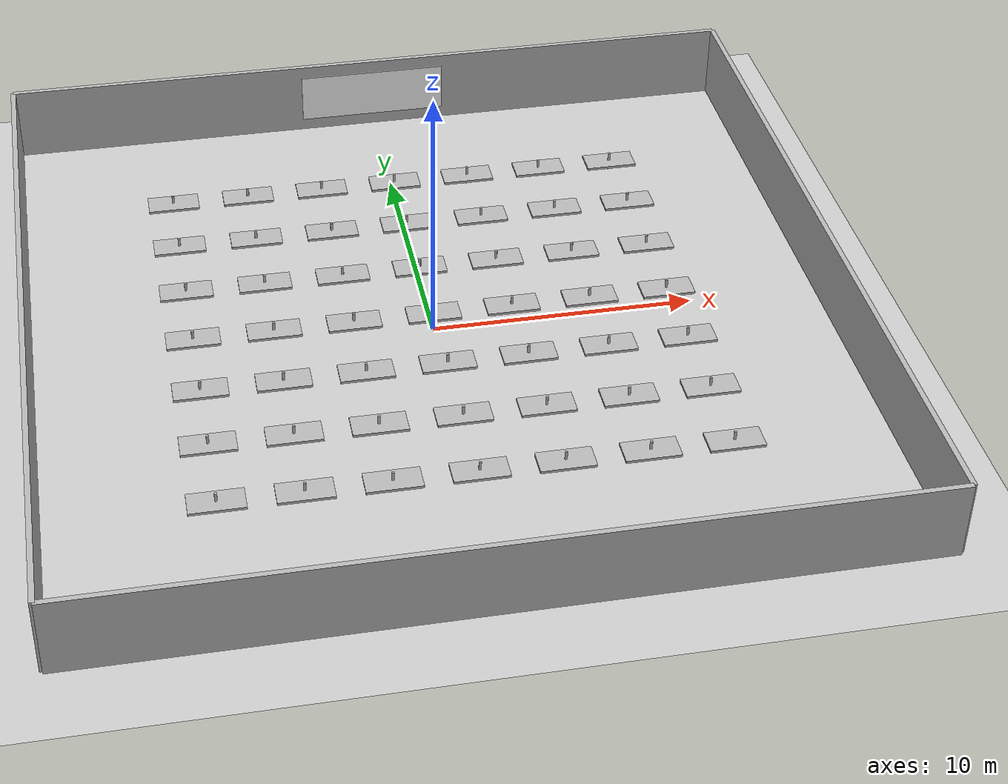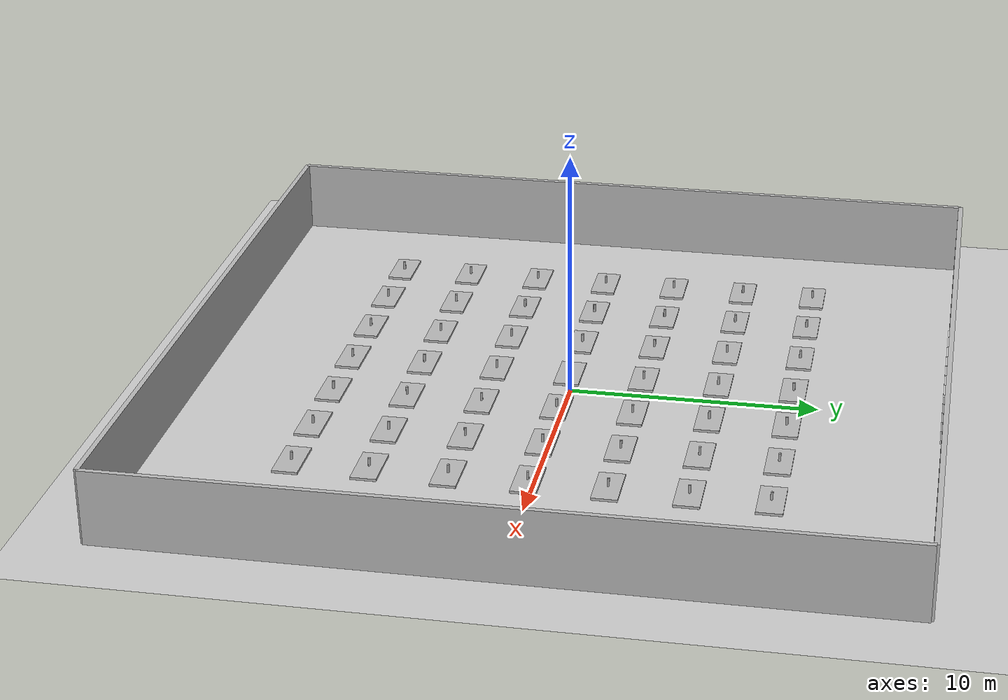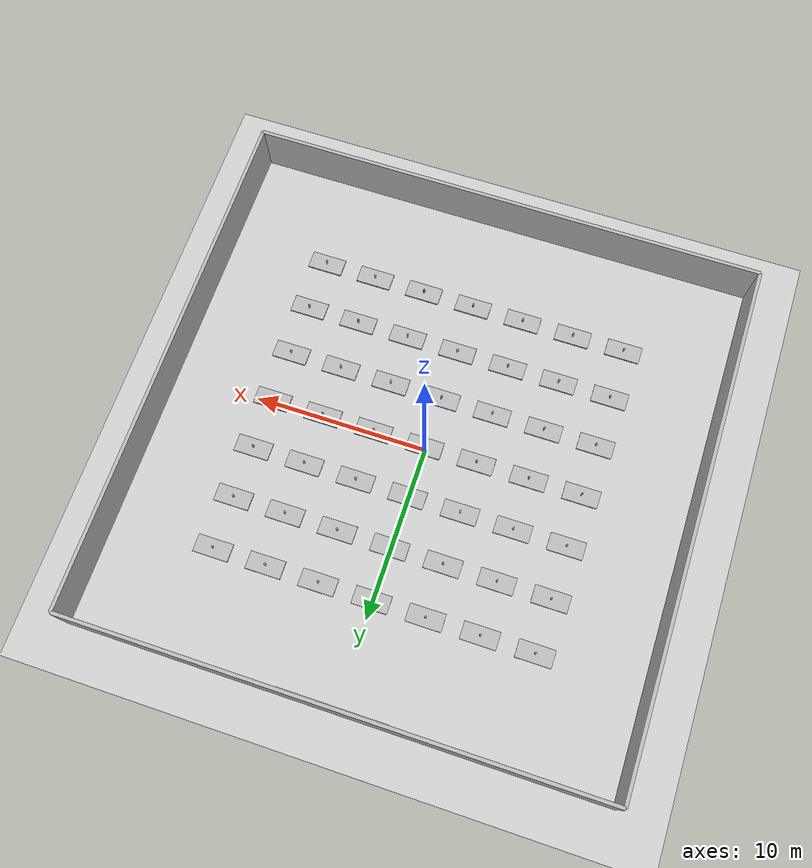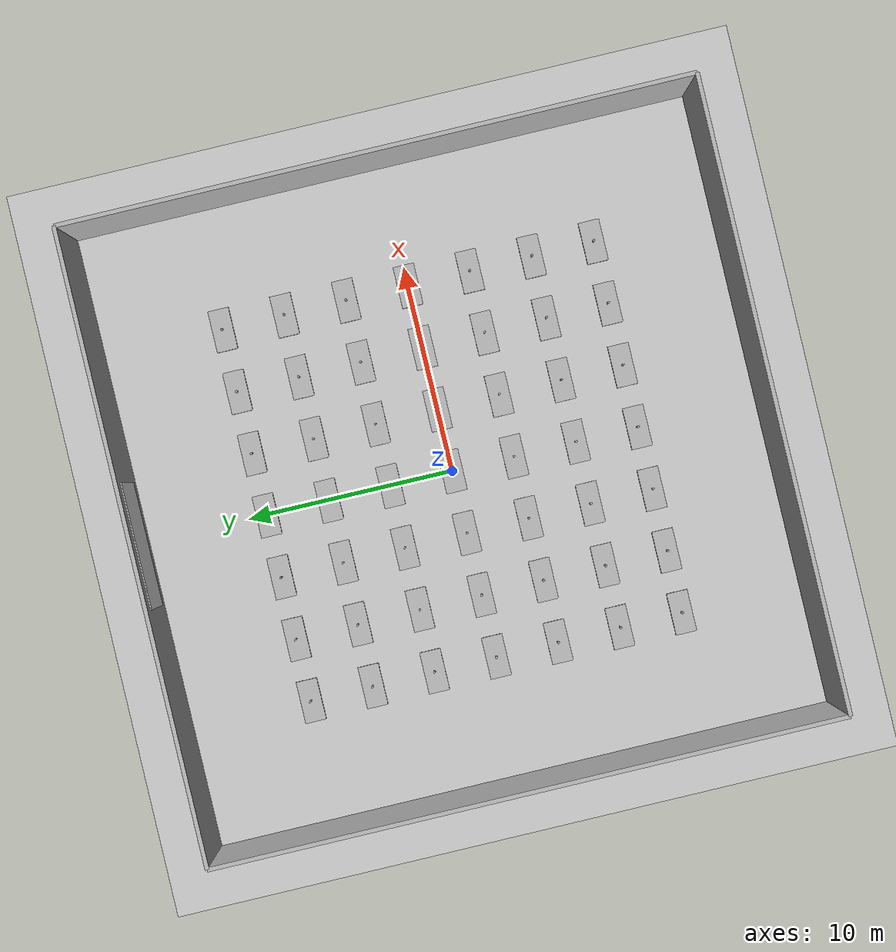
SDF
<sdf version="1.7">
 <world name="classroom_world">
  <light name="sun" type="directional">
   <pose>0 0 10 0 -0 0</pose>
   <diffuse>0.8 0.8 0.8 1</diffuse>
   <specular>0.2 0.2 0.2 1</specular>
   <attenuation>
    <range>1000</range>
    <constant>0.9</constant>
    <linear>0.01</linear>
    <quadratic>0.001</quadratic>
   </attenuation>
   <direction>-0.5 0.1 -0.9</direction>
   <spot><inner_angle>0</inner_angle><outer_angle>0</outer_angle><falloff>0</falloff></spot>
  </light>
  <model name="ground_plane">
   <static>1</static>
   <link name="link">
    <collision name="collision">
     <geometry><plane><normal>0 0 1</normal><size>100 100</size></plane></geometry>
     <surface><friction><ode><mu>100</mu><mu2>50</mu2></ode></friction></surface>
    </collision>
    <visual name="visual">
     <cast_shadows>0</cast_shadows>
     <geometry><plane><normal>0 0 1</normal><size>100 100</size></plane></geometry>
     <material>
      <script><uri>file://media/materials/scripts/gazebo.material</uri><name>Gazebo/Grey</name></script>
     </material>
    </visual>
   </link>
  </model>
  <model name="floor">
   <static>1</static>
   <link name="link">
    <collision name="collision"><geometry><box><size>30 30 0.1</size></box></geometry></collision>
    <visual name="visual">
     <geometry><box><size>30 30 0.1</size></box></geometry>
     <material><ambient>0.8 0.8 0.8 1</ambient></material>
    </visual>
    <pose>0 0 -0.05 0 -0 0</pose>
   </link>
  </model>
  <model name="north_wall">
   <static>1</static>
   <link name="link">
    <collision name="collision"><geometry><box><size>30 0.2 3</size></box></geometry></collision>
    <visual name="visual"><geometry><box><size>30 0.2 3</size></box></geometry></visual>
    <pose>0 15 1.5 0 -0 0</pose>
   </link>
  </model>
  <model name="south_wall">
   <static>1</static>
   <link name="link">
    <collision name="collision"><geometry><box><size>30 0.2 3</size></box></geometry></collision>
    <visual name="visual"><geometry><box><size>30 0.2 3</size></box></geometry></visual>
    <pose>0 -15 1.5 0 -0 0</pose>
   </link>
  </model>
  <model name="east_wall">
   <static>1</static>
   <link name="link">
    <collision name="collision"><geometry><box><size>0.2 30 3</size></box></geometry></collision>
    <visual name="visual"><geometry><box><size>0.2 30 3</size></box></geometry></visual>
    <pose>15 0 1.5 0 -0 0</pose>
   </link>
  </model>
  <model name="west_wall">
   <static>1</static>
   <link name="link">
    <collision name="collision"><geometry><box><size>0.2 30 3</size></box></geometry></collision>
    <visual name="visual"><geometry><box><size>0.2 30 3</size></box></geometry></visual>
    <pose>-15 0 1.5 0 -0 0</pose>
   </link>
  </model>
  <model name="whiteboard">
   <static>1</static>
   <link name="link">
    <collision name="col"><geometry><box><size>6 0.1 2</size></box></geometry></collision>
    <visual name="vis">
     <geometry><box><size>6 0.1 2</size></box></geometry>
     <material><ambient>1 1 1 1</ambient><diffuse>1 1 1 1</diffuse></material>
    </visual>
    <pose>0 14.9 1.5 0 -0 0</pose>
   </link>
  </model>
  <model name="table_r1_c1">
   <static>1</static>
   <link name="link">
    <visual name="top"><geometry><box><size>2 1 0.1</size></box></geometry></visual>
    <collision name="top_col"><geometry><box><size>2 1 0.1</size></box></geometry></collision>
    <pose>-9 -9 0.75 0 -0 0</pose>
    <visual name="leg1">
     <geometry><cylinder><radius>0.05</radius><length>0.75</length></cylinder></geometry>
    </visual>
    <collision name="leg1_col">
     <geometry><cylinder><radius>0.05</radius><length>0.75</length></cylinder></geometry>
    </collision>
    <pose>-10 -9.5 0.375 0 -0 0</pose>
    <visual name="leg2">
     <geometry><cylinder><radius>0.05</radius><length>0.75</length></cylinder></geometry>
    </visual>
    <collision name="leg2_col">
     <geometry><cylinder><radius>0.05</radius><length>0.75</length></cylinder></geometry>
    </collision>
    <pose>-8 -9.5 0.375 0 -0 0</pose>
    <visual name="leg3">
     <geometry><cylinder><radius>0.05</radius><length>0.75</length></cylinder></geometry>
    </visual>
    <collision name="leg3_col">
     <geometry><cylinder><radius>0.05</radius><length>0.75</length></cylinder></geometry>
    </collision>
    <pose>-10 -8.5 0.375 0 -0 0</pose>
    <visual name="leg4">
     <geometry><cylinder><radius>0.05</radius><length>0.75</length></cylinder></geometry>
    </visual>
    <collision name="leg4_col">
     <geometry><cylinder><radius>0.05</radius><length>0.75</length></cylinder></geometry>
    </collision>
    <pose>-8 -8.5 0.375 0 -0 0</pose>
   </link>
  </model>
  <model name="table_r1_c2">
   <static>1</static>
   <link name="link">
    <visual name="top"><geometry><box><size>2 1 0.1</size></box></geometry></visual>
    <collision name="top_col"><geometry><box><size>2 1 0.1</size></box></geometry></collision>
    <pose>-6 -9 0.75 0 -0 0</pose>
    <visual name="leg1">
     <geometry><cylinder><radius>0.05</radius><length>0.75</length></cylinder></geometry>
    </visual>
    <collision name="leg1_col">
     <geometry><cylinder><radius>0.05</radius><length>0.75</length></cylinder></geometry>
    </collision>
    <pose>-7 -9.5 0.375 0 -0 0</pose>
    <visual name="leg2">
     <geometry><cylinder><radius>0.05</radius><length>0.75</length></cylinder></geometry>
    </visual>
    <collision name="leg2_col">
     <geometry><cylinder><radius>0.05</radius><length>0.75</length></cylinder></geometry>
    </collision>
    <pose>-5 -9.5 0.375 0 -0 0</pose>
    <visual name="leg3">
     <geometry><cylinder><radius>0.05</radius><length>0.75</length></cylinder></geometry>
    </visual>
    <collision name="leg3_col">
     <geometry><cylinder><radius>0.05</radius><length>0.75</length></cylinder></geometry>
    </collision>
    <pose>-7 -8.5 0.375 0 -0 0</pose>
    <visual name="leg4">
     <geometry><cylinder><radius>0.05</radius><length>0.75</length></cylinder></geometry>
    </visual>
    <collision name="leg4_col">
     <geometry><cylinder><radius>0.05</radius><length>0.75</length></cylinder></geometry>
    </collision>
    <pose>-5 -8.5 0.375 0 -0 0</pose>
   </link>
  </model>
  <model name="table_r1_c3">
   <static>1</static>
   <link name="link">
    <visual name="top"><geometry><box><size>2 1 0.1</size></box></geometry></visual>
    <collision name="top_col"><geometry><box><size>2 1 0.1</size></box></geometry></collision>
    <pose>-3 -9 0.75 0 -0 0</pose>
    <visual name="leg1">
     <geometry><cylinder><radius>0.05</radius><length>0.75</length></cylinder></geometry>
    </visual>
    <collision name="leg1_col">
     <geometry><cylinder><radius>0.05</radius><length>0.75</length></cylinder></geometry>
    </collision>
    <pose>-4 -9.5 0.375 0 -0 0</pose>
    <visual name="leg2">
     <geometry><cylinder><radius>0.05</radius><length>0.75</length></cylinder></geometry>
    </visual>
    <collision name="leg2_col">
     <geometry><cylinder><radius>0.05</radius><length>0.75</length></cylinder></geometry>
    </collision>
    <pose>-2 -9.5 0.375 0 -0 0</pose>
    <visual name="leg3">
     <geometry><cylinder><radius>0.05</radius><length>0.75</length></cylinder></geometry>
    </visual>
    <collision name="leg3_col">
     <geometry><cylinder><radius>0.05</radius><length>0.75</length></cylinder></geometry>
    </collision>
    <pose>-4 -8.5 0.375 0 -0 0</pose>
    <visual name="leg4">
     <geometry><cylinder><radius>0.05</radius><length>0.75</length></cylinder></geometry>
    </visual>
    <collision name="leg4_col">
     <geometry><cylinder><radius>0.05</radius><length>0.75</length></cylinder></geometry>
    </collision>
    <pose>-2 -8.5 0.375 0 -0 0</pose>
   </link>
  </model>
  <model name="table_r1_c4">
   <static>1</static>
   <link name="link">
    <visual name="top"><geometry><box><size>2 1 0.1</size></box></geometry></visual>
    <collision name="top_col"><geometry><box><size>2 1 0.1</size></box></geometry></collision>
    <pose>0 -9 0.75 0 -0 0</pose>
    <visual name="leg1">
     <geometry><cylinder><radius>0.05</radius><length>0.75</length></cylinder></geometry>
    </visual>
    <collision name="leg1_col">
     <geometry><cylinder><radius>0.05</radius><length>0.75</length></cylinder></geometry>
    </collision>
    <pose>-1 -9.5 0.375 0 -0 0</pose>
    <visual name="leg2">
     <geometry><cylinder><radius>0.05</radius><length>0.75</length></cylinder></geometry>
    </visual>
    <collision name="leg2_col">
     <geometry><cylinder><radius>0.05</radius><length>0.75</length></cylinder></geometry>
    </collision>
    <pose>1 -9.5 0.375 0 -0 0</pose>
    <visual name="leg3">
     <geometry><cylinder><radius>0.05</radius><length>0.75</length></cylinder></geometry>
    </visual>
    <collision name="leg3_col">
     <geometry><cylinder><radius>0.05</radius><length>0.75</length></cylinder></geometry>
    </collision>
    <pose>-1 -8.5 0.375 0 -0 0</pose>
    <visual name="leg4">
     <geometry><cylinder><radius>0.05</radius><length>0.75</length></cylinder></geometry>
    </visual>
    <collision name="leg4_col">
     <geometry><cylinder><radius>0.05</radius><length>0.75</length></cylinder></geometry>
    </collision>
    <pose>1 -8.5 0.375 0 -0 0</pose>
   </link>
  </model>
  <model name="table_r1_c5">
   <static>1</static>
   <link name="link">
    <visual name="top"><geometry><box><size>2 1 0.1</size></box></geometry></visual>
    <collision name="top_col"><geometry><box><size>2 1 0.1</size></box></geometry></collision>
    <pose>3 -9 0.75 0 -0 0</pose>
    <visual name="leg1">
     <geometry><cylinder><radius>0.05</radius><length>0.75</length></cylinder></geometry>
    </visual>
    <collision name="leg1_col">
     <geometry><cylinder><radius>0.05</radius><length>0.75</length></cylinder></geometry>
    </collision>
    <pose>2 -9.5 0.375 0 -0 0</pose>
    <visual name="leg2">
     <geometry><cylinder><radius>0.05</radius><length>0.75</length></cylinder></geometry>
    </visual>
    <collision name="leg2_col">
     <geometry><cylinder><radius>0.05</radius><length>0.75</length></cylinder></geometry>
    </collision>
    <pose>4 -9.5 0.375 0 -0 0</pose>
    <visual name="leg3">
     <geometry><cylinder><radius>0.05</radius><length>0.75</length></cylinder></geometry>
    </visual>
    <collision name="leg3_col">
     <geometry><cylinder><radius>0.05</radius><length>0.75</length></cylinder></geometry>
    </collision>
    <pose>2 -8.5 0.375 0 -0 0</pose>
    <visual name="leg4">
     <geometry><cylinder><radius>0.05</radius><length>0.75</length></cylinder></geometry>
    </visual>
    <collision name="leg4_col">
     <geometry><cylinder><radius>0.05</radius><length>0.75</length></cylinder></geometry>
    </collision>
    <pose>4 -8.5 0.375 0 -0 0</pose>
   </link>
  </model>
  <model name="table_r1_c6">
   <static>1</static>
   <link name="link">
    <visual name="top"><geometry><box><size>2 1 0.1</size></box></geometry></visual>
    <collision name="top_col"><geometry><box><size>2 1 0.1</size></box></geometry></collision>
    <pose>6 -9 0.75 0 -0 0</pose>
    <visual name="leg1">
     <geometry><cylinder><radius>0.05</radius><length>0.75</length></cylinder></geometry>
    </visual>
    <collision name="leg1_col">
     <geometry><cylinder><radius>0.05</radius><length>0.75</length></cylinder></geometry>
    </collision>
    <pose>5 -9.5 0.375 0 -0 0</pose>
    <visual name="leg2">
     <geometry><cylinder><radius>0.05</radius><length>0.75</length></cylinder></geometry>
    </visual>
    <collision name="leg2_col">
     <geometry><cylinder><radius>0.05</radius><length>0.75</length></cylinder></geometry>
    </collision>
    <pose>7 -9.5 0.375 0 -0 0</pose>
    <visual name="leg3">
     <geometry><cylinder><radius>0.05</radius><length>0.75</length></cylinder></geometry>
    </visual>
    <collision name="leg3_col">
     <geometry><cylinder><radius>0.05</radius><length>0.75</length></cylinder></geometry>
    </collision>
    <pose>5 -8.5 0.375 0 -0 0</pose>
    <visual name="leg4">
     <geometry><cylinder><radius>0.05</radius><length>0.75</length></cylinder></geometry>
    </visual>
    <collision name="leg4_col">
     <geometry><cylinder><radius>0.05</radius><length>0.75</length></cylinder></geometry>
    </collision>
    <pose>7 -8.5 0.375 0 -0 0</pose>
   </link>
  </model>
  <model name="table_r1_c7">
   <static>1</static>
   <link name="link">
    <visual name="top"><geometry><box><size>2 1 0.1</size></box></geometry></visual>
    <collision name="top_col"><geometry><box><size>2 1 0.1</size></box></geometry></collision>
    <pose>9 -9 0.75 0 -0 0</pose>
    <visual name="leg1">
     <geometry><cylinder><radius>0.05</radius><length>0.75</length></cylinder></geometry>
    </visual>
    <collision name="leg1_col">
     <geometry><cylinder><radius>0.05</radius><length>0.75</length></cylinder></geometry>
    </collision>
    <pose>8 -9.5 0.375 0 -0 0</pose>
    <visual name="leg2">
     <geometry><cylinder><radius>0.05</radius><length>0.75</length></cylinder></geometry>
    </visual>
    <collision name="leg2_col">
     <geometry><cylinder><radius>0.05</radius><length>0.75</length></cylinder></geometry>
    </collision>
    <pose>10 -9.5 0.375 0 -0 0</pose>
    <visual name="leg3">
     <geometry><cylinder><radius>0.05</radius><length>0.75</length></cylinder></geometry>
    </visual>
    <collision name="leg3_col">
     <geometry><cylinder><radius>0.05</radius><length>0.75</length></cylinder></geometry>
    </collision>
    <pose>8 -8.5 0.375 0 -0 0</pose>
    <visual name="leg4">
     <geometry><cylinder><radius>0.05</radius><length>0.75</length></cylinder></geometry>
    </visual>
    <collision name="leg4_col">
     <geometry><cylinder><radius>0.05</radius><length>0.75</length></cylinder></geometry>
    </collision>
    <pose>10 -8.5 0.375 0 -0 0</pose>
   </link>
  </model>
  <model name="table_r2_c1">
   <static>1</static>
   <link name="link">
    <visual name="top"><geometry><box><size>2 1 0.1</size></box></geometry></visual>
    <collision name="top_col"><geometry><box><size>2 1 0.1</size></box></geometry></collision>
    <pose>-9 -6 0.75 0 -0 0</pose>
    <visual name="leg1">
     <geometry><cylinder><radius>0.05</radius><length>0.75</length></cylinder></geometry>
    </visual>
    <collision name="leg1_col">
     <geometry><cylinder><radius>0.05</radius><length>0.75</length></cylinder></geometry>
    </collision>
    <pose>-10 -6.5 0.375 0 -0 0</pose>
    <visual name="leg2">
     <geometry><cylinder><radius>0.05</radius><length>0.75</length></cylinder></geometry>
    </visual>
    <collision name="leg2_col">
     <geometry><cylinder><radius>0.05</radius><length>0.75</length></cylinder></geometry>
    </collision>
    <pose>-8 -6.5 0.375 0 -0 0</pose>
    <visual name="leg3">
     <geometry><cylinder><radius>0.05</radius><length>0.75</length></cylinder></geometry>
    </visual>
    <collision name="leg3_col">
     <geometry><cylinder><radius>0.05</radius><length>0.75</length></cylinder></geometry>
    </collision>
    <pose>-10 -5.5 0.375 0 -0 0</pose>
    <visual name="leg4">
     <geometry><cylinder><radius>0.05</radius><length>0.75</length></cylinder></geometry>
    </visual>
    <collision name="leg4_col">
     <geometry><cylinder><radius>0.05</radius><length>0.75</length></cylinder></geometry>
    </collision>
    <pose>-8 -5.5 0.375 0 -0 0</pose>
   </link>
  </model>
  <model name="table_r2_c2">
   <static>1</static>
   <link name="link">
    <visual name="top"><geometry><box><size>2 1 0.1</size></box></geometry></visual>
    <collision name="top_col"><geometry><box><size>2 1 0.1</size></box></geometry></collision>
    <pose>-6 -6 0.75 0 -0 0</pose>
    <visual name="leg1">
     <geometry><cylinder><radius>0.05</radius><length>0.75</length></cylinder></geometry>
    </visual>
    <collision name="leg1_col">
     <geometry><cylinder><radius>0.05</radius><length>0.75</length></cylinder></geometry>
    </collision>
    <pose>-7 -6.5 0.375 0 -0 0</pose>
    <visual name="leg2">
     <geometry><cylinder><radius>0.05</radius><length>0.75</length></cylinder></geometry>
    </visual>
    <collision name="leg2_col">
     <geometry><cylinder><radius>0.05</radius><length>0.75</length></cylinder></geometry>
    </collision>
    <pose>-5 -6.5 0.375 0 -0 0</pose>
    <visual name="leg3">
     <geometry><cylinder><radius>0.05</radius><length>0.75</length></cylinder></geometry>
    </visual>
    <collision name="leg3_col">
     <geometry><cylinder><radius>0.05</radius><length>0.75</length></cylinder></geometry>
    </collision>
    <pose>-7 -5.5 0.375 0 -0 0</pose>
    <visual name="leg4">
     <geometry><cylinder><radius>0.05</radius><length>0.75</length></cylinder></geometry>
    </visual>
    <collision name="leg4_col">
     <geometry><cylinder><radius>0.05</radius><length>0.75</length></cylinder></geometry>
    </collision>
    <pose>-5 -5.5 0.375 0 -0 0</pose>
   </link>
  </model>
  <model name="table_r2_c3">
   <static>1</static>
   <link name="link">
    <visual name="top"><geometry><box><size>2 1 0.1</size></box></geometry></visual>
    <collision name="top_col"><geometry><box><size>2 1 0.1</size></box></geometry></collision>
    <pose>-3 -6 0.75 0 -0 0</pose>
    <visual name="leg1">
     <geometry><cylinder><radius>0.05</radius><length>0.75</length></cylinder></geometry>
    </visual>
    <collision name="leg1_col">
     <geometry><cylinder><radius>0.05</radius><length>0.75</length></cylinder></geometry>
    </collision>
    <pose>-4 -6.5 0.375 0 -0 0</pose>
    <visual name="leg2">
     <geometry><cylinder><radius>0.05</radius><length>0.75</length></cylinder></geometry>
    </visual>
    <collision name="leg2_col">
     <geometry><cylinder><radius>0.05</radius><length>0.75</length></cylinder></geometry>
    </collision>
    <pose>-2 -6.5 0.375 0 -0 0</pose>
    <visual name="leg3">
     <geometry><cylinder><radius>0.05</radius><length>0.75</length></cylinder></geometry>
    </visual>
    <collision name="leg3_col">
     <geometry><cylinder><radius>0.05</radius><length>0.75</length></cylinder></geometry>
    </collision>
    <pose>-4 -5.5 0.375 0 -0 0</pose>
    <visual name="leg4">
     <geometry><cylinder><radius>0.05</radius><length>0.75</length></cylinder></geometry>
    </visual>
    <collision name="leg4_col">
     <geometry><cylinder><radius>0.05</radius><length>0.75</length></cylinder></geometry>
    </collision>
    <pose>-2 -5.5 0.375 0 -0 0</pose>
   </link>
  </model>
  <model name="table_r2_c4">
   <static>1</static>
   <link name="link">
    <visual name="top"><geometry><box><size>2 1 0.1</size></box></geometry></visual>
    <collision name="top_col"><geometry><box><size>2 1 0.1</size></box></geometry></collision>
    <pose>0 -6 0.75 0 -0 0</pose>
    <visual name="leg1">
     <geometry><cylinder><radius>0.05</radius><length>0.75</length></cylinder></geometry>
    </visual>
    <collision name="leg1_col">
     <geometry><cylinder><radius>0.05</radius><length>0.75</length></cylinder></geometry>
    </collision>
    <pose>-1 -6.5 0.375 0 -0 0</pose>
    <visual name="leg2">
     <geometry><cylinder><radius>0.05</radius><length>0.75</length></cylinder></geometry>
    </visual>
    <collision name="leg2_col">
     <geometry><cylinder><radius>0.05</radius><length>0.75</length></cylinder></geometry>
    </collision>
    <pose>1 -6.5 0.375 0 -0 0</pose>
    <visual name="leg3">
     <geometry><cylinder><radius>0.05</radius><length>0.75</length></cylinder></geometry>
    </visual>
    <collision name="leg3_col">
     <geometry><cylinder><radius>0.05</radius><length>0.75</length></cylinder></geometry>
    </collision>
    <pose>-1 -5.5 0.375 0 -0 0</pose>
    <visual name="leg4">
     <geometry><cylinder><radius>0.05</radius><length>0.75</length></cylinder></geometry>
    </visual>
    <collision name="leg4_col">
     <geometry><cylinder><radius>0.05</radius><length>0.75</length></cylinder></geometry>
    </collision>
    <pose>1 -5.5 0.375 0 -0 0</pose>
   </link>
  </model>
  <model name="table_r2_c5">
   <static>1</static>
   <link name="link">
    <visual name="top"><geometry><box><size>2 1 0.1</size></box></geometry></visual>
    <collision name="top_col"><geometry><box><size>2 1 0.1</size></box></geometry></collision>
    <pose>3 -6 0.75 0 -0 0</pose>
    <visual name="leg1">
     <geometry><cylinder><radius>0.05</radius><length>0.75</length></cylinder></geometry>
    </visual>
    <collision name="leg1_col">
     <geometry><cylinder><radius>0.05</radius><length>0.75</length></cylinder></geometry>
    </collision>
    <pose>2 -6.5 0.375 0 -0 0</pose>
    <visual name="leg2">
     <geometry><cylinder><radius>0.05</radius><length>0.75</length></cylinder></geometry>
    </visual>
    <collision name="leg2_col">
     <geometry><cylinder><radius>0.05</radius><length>0.75</length></cylinder></geometry>
    </collision>
    <pose>4 -6.5 0.375 0 -0 0</pose>
    <visual name="leg3">
     <geometry><cylinder><radius>0.05</radius><length>0.75</length></cylinder></geometry>
    </visual>
    <collision name="leg3_col">
     <geometry><cylinder><radius>0.05</radius><length>0.75</length></cylinder></geometry>
    </collision>
    <pose>2 -5.5 0.375 0 -0 0</pose>
    <visual name="leg4">
     <geometry><cylinder><radius>0.05</radius><length>0.75</length></cylinder></geometry>
    </visual>
    <collision name="leg4_col">
     <geometry><cylinder><radius>0.05</radius><length>0.75</length></cylinder></geometry>
    </collision>
    <pose>4 -5.5 0.375 0 -0 0</pose>
   </link>
  </model>
  <model name="table_r2_c6">
   <static>1</static>
   <link name="link">
    <visual name="top"><geometry><box><size>2 1 0.1</size></box></geometry></visual>
    <collision name="top_col"><geometry><box><size>2 1 0.1</size></box></geometry></collision>
    <pose>6 -6 0.75 0 -0 0</pose>
    <visual name="leg1">
     <geometry><cylinder><radius>0.05</radius><length>0.75</length></cylinder></geometry>
    </visual>
    <collision name="leg1_col">
     <geometry><cylinder><radius>0.05</radius><length>0.75</length></cylinder></geometry>
    </collision>
    <pose>5 -6.5 0.375 0 -0 0</pose>
    <visual name="leg2">
     <geometry><cylinder><radius>0.05</radius><length>0.75</length></cylinder></geometry>
    </visual>
    <collision name="leg2_col">
     <geometry><cylinder><radius>0.05</radius><length>0.75</length></cylinder></geometry>
    </collision>
    <pose>7 -6.5 0.375 0 -0 0</pose>
    <visual name="leg3">
     <geometry><cylinder><radius>0.05</radius><length>0.75</length></cylinder></geometry>
    </visual>
    <collision name="leg3_col">
     <geometry><cylinder><radius>0.05</radius><length>0.75</length></cylinder></geometry>
    </collision>
    <pose>5 -5.5 0.375 0 -0 0</pose>
    <visual name="leg4">
     <geometry><cylinder><radius>0.05</radius><length>0.75</length></cylinder></geometry>
    </visual>
    <collision name="leg4_col">
     <geometry><cylinder><radius>0.05</radius><length>0.75</length></cylinder></geometry>
    </collision>
    <pose>7 -5.5 0.375 0 -0 0</pose>
   </link>
  </model>
  <model name="table_r2_c7">
   <static>1</static>
   <link name="link">
    <visual name="top"><geometry><box><size>2 1 0.1</size></box></geometry></visual>
    <collision name="top_col"><geometry><box><size>2 1 0.1</size></box></geometry></collision>
    <pose>9 -6 0.75 0 -0 0</pose>
    <visual name="leg1">
     <geometry><cylinder><radius>0.05</radius><length>0.75</length></cylinder></geometry>
    </visual>
    <collision name="leg1_col">
     <geometry><cylinder><radius>0.05</radius><length>0.75</length></cylinder></geometry>
    </collision>
    <pose>8 -6.5 0.375 0 -0 0</pose>
    <visual name="leg2">
     <geometry><cylinder><radius>0.05</radius><length>0.75</length></cylinder></geometry>
    </visual>
    <collision name="leg2_col">
     <geometry><cylinder><radius>0.05</radius><length>0.75</length></cylinder></geometry>
    </collision>
    <pose>10 -6.5 0.375 0 -0 0</pose>
    <visual name="leg3">
     <geometry><cylinder><radius>0.05</radius><length>0.75</length></cylinder></geometry>
    </visual>
    <collision name="leg3_col">
     <geometry><cylinder><radius>0.05</radius><length>0.75</length></cylinder></geometry>
    </collision>
    <pose>8 -5.5 0.375 0 -0 0</pose>
    <visual name="leg4">
     <geometry><cylinder><radius>0.05</radius><length>0.75</length></cylinder></geometry>
    </visual>
    <collision name="leg4_col">
     <geometry><cylinder><radius>0.05</radius><length>0.75</length></cylinder></geometry>
    </collision>
    <pose>10 -5.5 0.375 0 -0 0</pose>
   </link>
  </model>
  <model name="table_r3_c1">
   <static>1</static>
   <link name="link">
    <visual name="top"><geometry><box><size>2 1 0.1</size></box></geometry></visual>
    <collision name="top_col"><geometry><box><size>2 1 0.1</size></box></geometry></collision>
    <pose>-9 -3 0.75 0 -0 0</pose>
    <visual name="leg1">
     <geometry><cylinder><radius>0.05</radius><length>0.75</length></cylinder></geometry>
    </visual>
    <collision name="leg1_col">
     <geometry><cylinder><radius>0.05</radius><length>0.75</length></cylinder></geometry>
    </collision>
    <pose>-10 -3.5 0.375 0 -0 0</pose>
    <visual name="leg2">
     <geometry><cylinder><radius>0.05</radius><length>0.75</length></cylinder></geometry>
    </visual>
    <collision name="leg2_col">
     <geometry><cylinder><radius>0.05</radius><length>0.75</length></cylinder></geometry>
    </collision>
    <pose>-8 -3.5 0.375 0 -0 0</pose>
    <visual name="leg3">
     <geometry><cylinder><radius>0.05</radius><length>0.75</length></cylinder></geometry>
    </visual>
    <collision name="leg3_col">
     <geometry><cylinder><radius>0.05</radius><length>0.75</length></cylinder></geometry>
    </collision>
    <pose>-10 -2.5 0.375 0 -0 0</pose>
    <visual name="leg4">
     <geometry><cylinder><radius>0.05</radius><length>0.75</length></cylinder></geometry>
    </visual>
    <collision name="leg4_col">
     <geometry><cylinder><radius>0.05</radius><length>0.75</length></cylinder></geometry>
    </collision>
    <pose>-8 -2.5 0.375 0 -0 0</pose>
   </link>
  </model>
  <model name="table_r3_c2">
   <static>1</static>
   <link name="link">
    <visual name="top"><geometry><box><size>2 1 0.1</size></box></geometry></visual>
    <collision name="top_col"><geometry><box><size>2 1 0.1</size></box></geometry></collision>
    <pose>-6 -3 0.75 0 -0 0</pose>
    <visual name="leg1">
     <geometry><cylinder><radius>0.05</radius><length>0.75</length></cylinder></geometry>
    </visual>
    <collision name="leg1_col">
     <geometry><cylinder><radius>0.05</radius><length>0.75</length></cylinder></geometry>
    </collision>
    <pose>-7 -3.5 0.375 0 -0 0</pose>
    <visual name="leg2">
     <geometry><cylinder><radius>0.05</radius><length>0.75</length></cylinder></geometry>
    </visual>
    <collision name="leg2_col">
     <geometry><cylinder><radius>0.05</radius><length>0.75</length></cylinder></geometry>
    </collision>
    <pose>-5 -3.5 0.375 0 -0 0</pose>
    <visual name="leg3">
     <geometry><cylinder><radius>0.05</radius><length>0.75</length></cylinder></geometry>
    </visual>
    <collision name="leg3_col">
     <geometry><cylinder><radius>0.05</radius><length>0.75</length></cylinder></geometry>
    </collision>
    <pose>-7 -2.5 0.375 0 -0 0</pose>
    <visual name="leg4">
     <geometry><cylinder><radius>0.05</radius><length>0.75</length></cylinder></geometry>
    </visual>
    <collision name="leg4_col">
     <geometry><cylinder><radius>0.05</radius><length>0.75</length></cylinder></geometry>
    </collision>
    <pose>-5 -2.5 0.375 0 -0 0</pose>
   </link>
  </model>
  <model name="table_r3_c3">
   <static>1</static>
   <link name="link">
    <visual name="top"><geometry><box><size>2 1 0.1</size></box></geometry></visual>
    <collision name="top_col"><geometry><box><size>2 1 0.1</size></box></geometry></collision>
    <pose>-3 -3 0.75 0 -0 0</pose>
    <visual name="leg1">
     <geometry><cylinder><radius>0.05</radius><length>0.75</length></cylinder></geometry>
    </visual>
    <collision name="leg1_col">
     <geometry><cylinder><radius>0.05</radius><length>0.75</length></cylinder></geometry>
    </collision>
    <pose>-4 -3.5 0.375 0 -0 0</pose>
    <visual name="leg2">
     <geometry><cylinder><radius>0.05</radius><length>0.75</length></cylinder></geometry>
    </visual>
    <collision name="leg2_col">
     <geometry><cylinder><radius>0.05</radius><length>0.75</length></cylinder></geometry>
    </collision>
    <pose>-2 -3.5 0.375 0 -0 0</pose>
    <visual name="leg3">
     <geometry><cylinder><radius>0.05</radius><length>0.75</length></cylinder></geometry>
    </visual>
    <collision name="leg3_col">
     <geometry><cylinder><radius>0.05</radius><length>0.75</length></cylinder></geometry>
    </collision>
    <pose>-4 -2.5 0.375 0 -0 0</pose>
    <visual name="leg4">
     <geometry><cylinder><radius>0.05</radius><length>0.75</length></cylinder></geometry>
    </visual>
    <collision name="leg4_col">
     <geometry><cylinder><radius>0.05</radius><length>0.75</length></cylinder></geometry>
    </collision>
    <pose>-2 -2.5 0.375 0 -0 0</pose>
   </link>
  </model>
  <model name="table_r3_c4">
   <static>1</static>
   <link name="link">
    <visual name="top"><geometry><box><size>2 1 0.1</size></box></geometry></visual>
    <collision name="top_col"><geometry><box><size>2 1 0.1</size></box></geometry></collision>
    <pose>0 -3 0.75 0 -0 0</pose>
    <visual name="leg1">
     <geometry><cylinder><radius>0.05</radius><length>0.75</length></cylinder></geometry>
    </visual>
    <collision name="leg1_col">
     <geometry><cylinder><radius>0.05</radius><length>0.75</length></cylinder></geometry>
    </collision>
    <pose>-1 -3.5 0.375 0 -0 0</pose>
    <visual name="leg2">
     <geometry><cylinder><radius>0.05</radius><length>0.75</length></cylinder></geometry>
    </visual>
    <collision name="leg2_col">
     <geometry><cylinder><radius>0.05</radius><length>0.75</length></cylinder></geometry>
    </collision>
    <pose>1 -3.5 0.375 0 -0 0</pose>
    <visual name="leg3">
     <geometry><cylinder><radius>0.05</radius><length>0.75</length></cylinder></geometry>
    </visual>
    <collision name="leg3_col">
     <geometry><cylinder><radius>0.05</radius><length>0.75</length></cylinder></geometry>
    </collision>
    <pose>-1 -2.5 0.375 0 -0 0</pose>
    <visual name="leg4">
     <geometry><cylinder><radius>0.05</radius><length>0.75</length></cylinder></geometry>
    </visual>
    <collision name="leg4_col">
     <geometry><cylinder><radius>0.05</radius><length>0.75</length></cylinder></geometry>
    </collision>
    <pose>1 -2.5 0.375 0 -0 0</pose>
   </link>
  </model>
  <model name="table_r3_c5">
   <static>1</static>
   <link name="link">
    <visual name="top"><geometry><box><size>2 1 0.1</size></box></geometry></visual>
    <collision name="top_col"><geometry><box><size>2 1 0.1</size></box></geometry></collision>
    <pose>3 -3 0.75 0 -0 0</pose>
    <visual name="leg1">
     <geometry><cylinder><radius>0.05</radius><length>0.75</length></cylinder></geometry>
    </visual>
    <collision name="leg1_col">
     <geometry><cylinder><radius>0.05</radius><length>0.75</length></cylinder></geometry>
    </collision>
    <pose>2 -3.5 0.375 0 -0 0</pose>
    <visual name="leg2">
     <geometry><cylinder><radius>0.05</radius><length>0.75</length></cylinder></geometry>
    </visual>
    <collision name="leg2_col">
     <geometry><cylinder><radius>0.05</radius><length>0.75</length></cylinder></geometry>
    </collision>
    <pose>4 -3.5 0.375 0 -0 0</pose>
    <visual name="leg3">
     <geometry><cylinder><radius>0.05</radius><length>0.75</length></cylinder></geometry>
    </visual>
    <collision name="leg3_col">
     <geometry><cylinder><radius>0.05</radius><length>0.75</length></cylinder></geometry>
    </collision>
    <pose>2 -2.5 0.375 0 -0 0</pose>
    <visual name="leg4">
     <geometry><cylinder><radius>0.05</radius><length>0.75</length></cylinder></geometry>
    </visual>
    <collision name="leg4_col">
     <geometry><cylinder><radius>0.05</radius><length>0.75</length></cylinder></geometry>
    </collision>
    <pose>4 -2.5 0.375 0 -0 0</pose>
   </link>
  </model>
  <model name="table_r3_c6">
   <static>1</static>
   <link name="link">
    <visual name="top"><geometry><box><size>2 1 0.1</size></box></geometry></visual>
    <collision name="top_col"><geometry><box><size>2 1 0.1</size></box></geometry></collision>
    <pose>6 -3 0.75 0 -0 0</pose>
    <visual name="leg1">
     <geometry><cylinder><radius>0.05</radius><length>0.75</length></cylinder></geometry>
    </visual>
    <collision name="leg1_col">
     <geometry><cylinder><radius>0.05</radius><length>0.75</length></cylinder></geometry>
    </collision>
    <pose>5 -3.5 0.375 0 -0 0</pose>
    <visual name="leg2">
     <geometry><cylinder><radius>0.05</radius><length>0.75</length></cylinder></geometry>
    </visual>
    <collision name="leg2_col">
     <geometry><cylinder><radius>0.05</radius><length>0.75</length></cylinder></geometry>
    </collision>
    <pose>7 -3.5 0.375 0 -0 0</pose>
    <visual name="leg3">
     <geometry><cylinder><radius>0.05</radius><length>0.75</length></cylinder></geometry>
    </visual>
    <collision name="leg3_col">
     <geometry><cylinder><radius>0.05</radius><length>0.75</length></cylinder></geometry>
    </collision>
    <pose>5 -2.5 0.375 0 -0 0</pose>
    <visual name="leg4">
     <geometry><cylinder><radius>0.05</radius><length>0.75</length></cylinder></geometry>
    </visual>
    <collision name="leg4_col">
     <geometry><cylinder><radius>0.05</radius><length>0.75</length></cylinder></geometry>
    </collision>
    <pose>7 -2.5 0.375 0 -0 0</pose>
   </link>
  </model>
  <model name="table_r3_c7">
   <static>1</static>
   <link name="link">
    <visual name="top"><geometry><box><size>2 1 0.1</size></box></geometry></visual>
    <collision name="top_col"><geometry><box><size>2 1 0.1</size></box></geometry></collision>
    <pose>9 -3 0.75 0 -0 0</pose>
    <visual name="leg1">
     <geometry><cylinder><radius>0.05</radius><length>0.75</length></cylinder></geometry>
    </visual>
    <collision name="leg1_col">
     <geometry><cylinder><radius>0.05</radius><length>0.75</length></cylinder></geometry>
    </collision>
    <pose>8 -3.5 0.375 0 -0 0</pose>
    <visual name="leg2">
     <geometry><cylinder><radius>0.05</radius><length>0.75</length></cylinder></geometry>
    </visual>
    <collision name="leg2_col">
     <geometry><cylinder><radius>0.05</radius><length>0.75</length></cylinder></geometry>
    </collision>
    <pose>10 -3.5 0.375 0 -0 0</pose>
    <visual name="leg3">
     <geometry><cylinder><radius>0.05</radius><length>0.75</length></cylinder></geometry>
    </visual>
    <collision name="leg3_col">
     <geometry><cylinder><radius>0.05</radius><length>0.75</length></cylinder></geometry>
    </collision>
    <pose>8 -2.5 0.375 0 -0 0</pose>
    <visual name="leg4">
     <geometry><cylinder><radius>0.05</radius><length>0.75</length></cylinder></geometry>
    </visual>
    <collision name="leg4_col">
     <geometry><cylinder><radius>0.05</radius><length>0.75</length></cylinder></geometry>
    </collision>
    <pose>10 -2.5 0.375 0 -0 0</pose>
   </link>
  </model>
  <model name="table_r4_c1">
   <static>1</static>
   <link name="link">
    <visual name="top"><geometry><box><size>2 1 0.1</size></box></geometry></visual>
    <collision name="top_col"><geometry><box><size>2 1 0.1</size></box></geometry></collision>
    <pose>-9 0 0.75 0 -0 0</pose>
    <visual name="leg1">
     <geometry><cylinder><radius>0.05</radius><length>0.75</length></cylinder></geometry>
    </visual>
    <collision name="leg1_col">
     <geometry><cylinder><radius>0.05</radius><length>0.75</length></cylinder></geometry>
    </collision>
    <pose>-10 -0.5 0.375 0 -0 0</pose>
    <visual name="leg2">
     <geometry><cylinder><radius>0.05</radius><length>0.75</length></cylinder></geometry>
    </visual>
    <collision name="leg2_col">
     <geometry><cylinder><radius>0.05</radius><length>0.75</length></cylinder></geometry>
    </collision>
    <pose>-8 -0.5 0.375 0 -0 0</pose>
    <visual name="leg3">
     <geometry><cylinder><radius>0.05</radius><length>0.75</length></cylinder></geometry>
    </visual>
    <collision name="leg3_col">
     <geometry><cylinder><radius>0.05</radius><length>0.75</length></cylinder></geometry>
    </collision>
    <pose>-10 0.5 0.375 0 -0 0</pose>
    <visual name="leg4">
     <geometry><cylinder><radius>0.05</radius><length>0.75</length></cylinder></geometry>
    </visual>
    <collision name="leg4_col">
     <geometry><cylinder><radius>0.05</radius><length>0.75</length></cylinder></geometry>
    </collision>
    <pose>-8 0.5 0.375 0 -0 0</pose>
   </link>
  </model>
  <model name="table_r4_c2">
   <static>1</static>
   <link name="link">
    <visual name="top"><geometry><box><size>2 1 0.1</size></box></geometry></visual>
    <collision name="top_col"><geometry><box><size>2 1 0.1</size></box></geometry></collision>
    <pose>-6 0 0.75 0 -0 0</pose>
    <visual name="leg1">
     <geometry><cylinder><radius>0.05</radius><length>0.75</length></cylinder></geometry>
    </visual>
    <collision name="leg1_col">
     <geometry><cylinder><radius>0.05</radius><length>0.75</length></cylinder></geometry>
    </collision>
    <pose>-7 -0.5 0.375 0 -0 0</pose>
    <visual name="leg2">
     <geometry><cylinder><radius>0.05</radius><length>0.75</length></cylinder></geometry>
    </visual>
    <collision name="leg2_col">
     <geometry><cylinder><radius>0.05</radius><length>0.75</length></cylinder></geometry>
    </collision>
    <pose>-5 -0.5 0.375 0 -0 0</pose>
    <visual name="leg3">
     <geometry><cylinder><radius>0.05</radius><length>0.75</length></cylinder></geometry>
    </visual>
    <collision name="leg3_col">
     <geometry><cylinder><radius>0.05</radius><length>0.75</length></cylinder></geometry>
    </collision>
    <pose>-7 0.5 0.375 0 -0 0</pose>
    <visual name="leg4">
     <geometry><cylinder><radius>0.05</radius><length>0.75</length></cylinder></geometry>
    </visual>
    <collision name="leg4_col">
     <geometry><cylinder><radius>0.05</radius><length>0.75</length></cylinder></geometry>
    </collision>
    <pose>-5 0.5 0.375 0 -0 0</pose>
   </link>
  </model>
  <model name="table_r4_c3">
   <static>1</static>
   <link name="link">
    <visual name="top"><geometry><box><size>2 1 0.1</size></box></geometry></visual>
    <collision name="top_col"><geometry><box><size>2 1 0.1</size></box></geometry></collision>
    <pose>-3 0 0.75 0 -0 0</pose>
    <visual name="leg1">
     <geometry><cylinder><radius>0.05</radius><length>0.75</length></cylinder></geometry>
    </visual>
    <collision name="leg1_col">
     <geometry><cylinder><radius>0.05</radius><length>0.75</length></cylinder></geometry>
    </collision>
    <pose>-4 -0.5 0.375 0 -0 0</pose>
    <visual name="leg2">
     <geometry><cylinder><radius>0.05</radius><length>0.75</length></cylinder></geometry>
    </visual>
    <collision name="leg2_col">
     <geometry><cylinder><radius>0.05</radius><length>0.75</length></cylinder></geometry>
    </collision>
    <pose>-2 -0.5 0.375 0 -0 0</pose>
    <visual name="leg3">
     <geometry><cylinder><radius>0.05</radius><length>0.75</length></cylinder></geometry>
    </visual>
    <collision name="leg3_col">
     <geometry><cylinder><radius>0.05</radius><length>0.75</length></cylinder></geometry>
    </collision>
    <pose>-4 0.5 0.375 0 -0 0</pose>
    <visual name="leg4">
     <geometry><cylinder><radius>0.05</radius><length>0.75</length></cylinder></geometry>
    </visual>
    <collision name="leg4_col">
     <geometry><cylinder><radius>0.05</radius><length>0.75</length></cylinder></geometry>
    </collision>
    <pose>-2 0.5 0.375 0 -0 0</pose>
   </link>
  </model>
  <model name="table_r4_c4">
   <static>1</static>
   <link name="link">
    <visual name="top"><geometry><box><size>2 1 0.1</size></box></geometry></visual>
    <collision name="top_col"><geometry><box><size>2 1 0.1</size></box></geometry></collision>
    <pose>0 0 0.75 0 -0 0</pose>
    <visual name="leg1">
     <geometry><cylinder><radius>0.05</radius><length>0.75</length></cylinder></geometry>
    </visual>
    <collision name="leg1_col">
     <geometry><cylinder><radius>0.05</radius><length>0.75</length></cylinder></geometry>
    </collision>
    <pose>-1 -0.5 0.375 0 -0 0</pose>
    <visual name="leg2">
     <geometry><cylinder><radius>0.05</radius><length>0.75</length></cylinder></geometry>
    </visual>
    <collision name="leg2_col">
     <geometry><cylinder><radius>0.05</radius><length>0.75</length></cylinder></geometry>
    </collision>
    <pose>1 -0.5 0.375 0 -0 0</pose>
    <visual name="leg3">
     <geometry><cylinder><radius>0.05</radius><length>0.75</length></cylinder></geometry>
    </visual>
    <collision name="leg3_col">
     <geometry><cylinder><radius>0.05</radius><length>0.75</length></cylinder></geometry>
    </collision>
    <pose>-1 0.5 0.375 0 -0 0</pose>
    <visual name="leg4">
     <geometry><cylinder><radius>0.05</radius><length>0.75</length></cylinder></geometry>
    </visual>
    <collision name="leg4_col">
     <geometry><cylinder><radius>0.05</radius><length>0.75</length></cylinder></geometry>
    </collision>
    <pose>1 0.5 0.375 0 -0 0</pose>
   </link>
  </model>
  <model name="table_r4_c5">
   <static>1</static>
   <link name="link">
    <visual name="top"><geometry><box><size>2 1 0.1</size></box></geometry></visual>
    <collision name="top_col"><geometry><box><size>2 1 0.1</size></box></geometry></collision>
    <pose>3 0 0.75 0 -0 0</pose>
    <visual name="leg1">
     <geometry><cylinder><radius>0.05</radius><length>0.75</length></cylinder></geometry>
    </visual>
    <collision name="leg1_col">
     <geometry><cylinder><radius>0.05</radius><length>0.75</length></cylinder></geometry>
    </collision>
    <pose>2 -0.5 0.375 0 -0 0</pose>
    <visual name="leg2">
     <geometry><cylinder><radius>0.05</radius><length>0.75</length></cylinder></geometry>
    </visual>
    <collision name="leg2_col">
     <geometry><cylinder><radius>0.05</radius><length>0.75</length></cylinder></geometry>
    </collision>
    <pose>4 -0.5 0.375 0 -0 0</pose>
    <visual name="leg3">
     <geometry><cylinder><radius>0.05</radius><length>0.75</length></cylinder></geometry>
    </visual>
    <collision name="leg3_col">
     <geometry><cylinder><radius>0.05</radius><length>0.75</length></cylinder></geometry>
    </collision>
    <pose>2 0.5 0.375 0 -0 0</pose>
    <visual name="leg4">
     <geometry><cylinder><radius>0.05</radius><length>0.75</length></cylinder></geometry>
    </visual>
    <collision name="leg4_col">
     <geometry><cylinder><radius>0.05</radius><length>0.75</length></cylinder></geometry>
    </collision>
    <pose>4 0.5 0.375 0 -0 0</pose>
   </link>
  </model>
  <model name="table_r4_c6">
   <static>1</static>
   <link name="link">
    <visual name="top"><geometry><box><size>2 1 0.1</size></box></geometry></visual>
    <collision name="top_col"><geometry><box><size>2 1 0.1</size></box></geometry></collision>
    <pose>6 0 0.75 0 -0 0</pose>
    <visual name="leg1">
     <geometry><cylinder><radius>0.05</radius><length>0.75</length></cylinder></geometry>
    </visual>
    <collision name="leg1_col">
     <geometry><cylinder><radius>0.05</radius><length>0.75</length></cylinder></geometry>
    </collision>
    <pose>5 -0.5 0.375 0 -0 0</pose>
    <visual name="leg2">
     <geometry><cylinder><radius>0.05</radius><length>0.75</length></cylinder></geometry>
    </visual>
    <collision name="leg2_col">
     <geometry><cylinder><radius>0.05</radius><length>0.75</length></cylinder></geometry>
    </collision>
    <pose>7 -0.5 0.375 0 -0 0</pose>
    <visual name="leg3">
     <geometry><cylinder><radius>0.05</radius><length>0.75</length></cylinder></geometry>
    </visual>
    <collision name="leg3_col">
     <geometry><cylinder><radius>0.05</radius><length>0.75</length></cylinder></geometry>
    </collision>
    <pose>5 0.5 0.375 0 -0 0</pose>
    <visual name="leg4">
     <geometry><cylinder><radius>0.05</radius><length>0.75</length></cylinder></geometry>
    </visual>
    <collision name="leg4_col">
     <geometry><cylinder><radius>0.05</radius><length>0.75</length></cylinder></geometry>
    </collision>
    <pose>7 0.5 0.375 0 -0 0</pose>
   </link>
  </model>
  <model name="table_r4_c7">
   <static>1</static>
   <link name="link">
    <visual name="top"><geometry><box><size>2 1 0.1</size></box></geometry></visual>
    <collision name="top_col"><geometry><box><size>2 1 0.1</size></box></geometry></collision>
    <pose>9 0 0.75 0 -0 0</pose>
    <visual name="leg1">
     <geometry><cylinder><radius>0.05</radius><length>0.75</length></cylinder></geometry>
    </visual>
    <collision name="leg1_col">
     <geometry><cylinder><radius>0.05</radius><length>0.75</length></cylinder></geometry>
    </collision>
    <pose>8 -0.5 0.375 0 -0 0</pose>
    <visual name="leg2">
     <geometry><cylinder><radius>0.05</radius><length>0.75</length></cylinder></geometry>
    </visual>
    <collision name="leg2_col">
     <geometry><cylinder><radius>0.05</radius><length>0.75</length></cylinder></geometry>
    </collision>
    <pose>10 -0.5 0.375 0 -0 0</pose>
    <visual name="leg3">
     <geometry><cylinder><radius>0.05</radius><length>0.75</length></cylinder></geometry>
    </visual>
    <collision name="leg3_col">
     <geometry><cylinder><radius>0.05</radius><length>0.75</length></cylinder></geometry>
    </collision>
    <pose>8 0.5 0.375 0 -0 0</pose>
    <visual name="leg4">
     <geometry><cylinder><radius>0.05</radius><length>0.75</length></cylinder></geometry>
    </visual>
    <collision name="leg4_col">
     <geometry><cylinder><radius>0.05</radius><length>0.75</length></cylinder></geometry>
    </collision>
    <pose>10 0.5 0.375 0 -0 0</pose>
   </link>
  </model>
  <model name="table_r5_c1">
   <static>1</static>
   <link name="link">
    <visual name="top"><geometry><box><size>2 1 0.1</size></box></geometry></visual>
    <collision name="top_col"><geometry><box><size>2 1 0.1</size></box></geometry></collision>
    <pose>-9 3 0.75 0 -0 0</pose>
    <visual name="leg1">
     <geometry><cylinder><radius>0.05</radius><length>0.75</length></cylinder></geometry>
    </visual>
    <collision name="leg1_col">
     <geometry><cylinder><radius>0.05</radius><length>0.75</length></cylinder></geometry>
    </collision>
    <pose>-10 2.5 0.375 0 -0 0</pose>
    <visual name="leg2">
     <geometry><cylinder><radius>0.05</radius><length>0.75</length></cylinder></geometry>
    </visual>
    <collision name="leg2_col">
     <geometry><cylinder><radius>0.05</radius><length>0.75</length></cylinder></geometry>
    </collision>
    <pose>-8 2.5 0.375 0 -0 0</pose>
    <visual name="leg3">
     <geometry><cylinder><radius>0.05</radius><length>0.75</length></cylinder></geometry>
    </visual>
    <collision name="leg3_col">
     <geometry><cylinder><radius>0.05</radius><length>0.75</length></cylinder></geometry>
    </collision>
    <pose>-10 3.5 0.375 0 -0 0</pose>
    <visual name="leg4">
     <geometry><cylinder><radius>0.05</radius><length>0.75</length></cylinder></geometry>
    </visual>
    <collision name="leg4_col">
     <geometry><cylinder><radius>0.05</radius><length>0.75</length></cylinder></geometry>
    </collision>
    <pose>-8 3.5 0.375 0 -0 0</pose>
   </link>
  </model>
  <model name="table_r5_c2">
   <static>1</static>
   <link name="link">
    <visual name="top"><geometry><box><size>2 1 0.1</size></box></geometry></visual>
    <collision name="top_col"><geometry><box><size>2 1 0.1</size></box></geometry></collision>
    <pose>-6 3 0.75 0 -0 0</pose>
    <visual name="leg1">
     <geometry><cylinder><radius>0.05</radius><length>0.75</length></cylinder></geometry>
    </visual>
    <collision name="leg1_col">
     <geometry><cylinder><radius>0.05</radius><length>0.75</length></cylinder></geometry>
    </collision>
    <pose>-7 2.5 0.375 0 -0 0</pose>
    <visual name="leg2">
     <geometry><cylinder><radius>0.05</radius><length>0.75</length></cylinder></geometry>
    </visual>
    <collision name="leg2_col">
     <geometry><cylinder><radius>0.05</radius><length>0.75</length></cylinder></geometry>
    </collision>
    <pose>-5 2.5 0.375 0 -0 0</pose>
    <visual name="leg3">
     <geometry><cylinder><radius>0.05</radius><length>0.75</length></cylinder></geometry>
    </visual>
    <collision name="leg3_col">
     <geometry><cylinder><radius>0.05</radius><length>0.75</length></cylinder></geometry>
    </collision>
    <pose>-7 3.5 0.375 0 -0 0</pose>
    <visual name="leg4">
     <geometry><cylinder><radius>0.05</radius><length>0.75</length></cylinder></geometry>
    </visual>
    <collision name="leg4_col">
     <geometry><cylinder><radius>0.05</radius><length>0.75</length></cylinder></geometry>
    </collision>
    <pose>-5 3.5 0.375 0 -0 0</pose>
   </link>
  </model>
  <model name="table_r5_c3">
   <static>1</static>
   <link name="link">
    <visual name="top"><geometry><box><size>2 1 0.1</size></box></geometry></visual>
    <collision name="top_col"><geometry><box><size>2 1 0.1</size></box></geometry></collision>
    <pose>-3 3 0.75 0 -0 0</pose>
    <visual name="leg1">
     <geometry><cylinder><radius>0.05</radius><length>0.75</length></cylinder></geometry>
    </visual>
    <collision name="leg1_col">
     <geometry><cylinder><radius>0.05</radius><length>0.75</length></cylinder></geometry>
    </collision>
    <pose>-4 2.5 0.375 0 -0 0</pose>
    <visual name="leg2">
     <geometry><cylinder><radius>0.05</radius><length>0.75</length></cylinder></geometry>
    </visual>
    <collision name="leg2_col">
     <geometry><cylinder><radius>0.05</radius><length>0.75</length></cylinder></geometry>
    </collision>
    <pose>-2 2.5 0.375 0 -0 0</pose>
    <visual name="leg3">
     <geometry><cylinder><radius>0.05</radius><length>0.75</length></cylinder></geometry>
    </visual>
    <collision name="leg3_col">
     <geometry><cylinder><radius>0.05</radius><length>0.75</length></cylinder></geometry>
    </collision>
    <pose>-4 3.5 0.375 0 -0 0</pose>
    <visual name="leg4">
     <geometry><cylinder><radius>0.05</radius><length>0.75</length></cylinder></geometry>
    </visual>
    <collision name="leg4_col">
     <geometry><cylinder><radius>0.05</radius><length>0.75</length></cylinder></geometry>
    </collision>
    <pose>-2 3.5 0.375 0 -0 0</pose>
   </link>
  </model>
  <model name="table_r5_c4">
   <static>1</static>
   <link name="link">
    <visual name="top"><geometry><box><size>2 1 0.1</size></box></geometry></visual>
    <collision name="top_col"><geometry><box><size>2 1 0.1</size></box></geometry></collision>
    <pose>0 3 0.75 0 -0 0</pose>
    <visual name="leg1">
     <geometry><cylinder><radius>0.05</radius><length>0.75</length></cylinder></geometry>
    </visual>
    <collision name="leg1_col">
     <geometry><cylinder><radius>0.05</radius><length>0.75</length></cylinder></geometry>
    </collision>
    <pose>-1 2.5 0.375 0 -0 0</pose>
    <visual name="leg2">
     <geometry><cylinder><radius>0.05</radius><length>0.75</length></cylinder></geometry>
    </visual>
    <collision name="leg2_col">
     <geometry><cylinder><radius>0.05</radius><length>0.75</length></cylinder></geometry>
    </collision>
    <pose>1 2.5 0.375 0 -0 0</pose>
    <visual name="leg3">
     <geometry><cylinder><radius>0.05</radius><length>0.75</length></cylinder></geometry>
    </visual>
    <collision name="leg3_col">
     <geometry><cylinder><radius>0.05</radius><length>0.75</length></cylinder></geometry>
    </collision>
    <pose>-1 3.5 0.375 0 -0 0</pose>
    <visual name="leg4">
     <geometry><cylinder><radius>0.05</radius><length>0.75</length></cylinder></geometry>
    </visual>
    <collision name="leg4_col">
     <geometry><cylinder><radius>0.05</radius><length>0.75</length></cylinder></geometry>
    </collision>
    <pose>1 3.5 0.375 0 -0 0</pose>
   </link>
  </model>
  <model name="table_r5_c5">
   <static>1</static>
   <link name="link">
    <visual name="top"><geometry><box><size>2 1 0.1</size></box></geometry></visual>
    <collision name="top_col"><geometry><box><size>2 1 0.1</size></box></geometry></collision>
    <pose>3 3 0.75 0 -0 0</pose>
    <visual name="leg1">
     <geometry><cylinder><radius>0.05</radius><length>0.75</length></cylinder></geometry>
    </visual>
    <collision name="leg1_col">
     <geometry><cylinder><radius>0.05</radius><length>0.75</length></cylinder></geometry>
    </collision>
    <pose>2 2.5 0.375 0 -0 0</pose>
    <visual name="leg2">
     <geometry><cylinder><radius>0.05</radius><length>0.75</length></cylinder></geometry>
    </visual>
    <collision name="leg2_col">
     <geometry><cylinder><radius>0.05</radius><length>0.75</length></cylinder></geometry>
    </collision>
    <pose>4 2.5 0.375 0 -0 0</pose>
    <visual name="leg3">
     <geometry><cylinder><radius>0.05</radius><length>0.75</length></cylinder></geometry>
    </visual>
    <collision name="leg3_col">
     <geometry><cylinder><radius>0.05</radius><length>0.75</length></cylinder></geometry>
    </collision>
    <pose>2 3.5 0.375 0 -0 0</pose>
    <visual name="leg4">
     <geometry><cylinder><radius>0.05</radius><length>0.75</length></cylinder></geometry>
    </visual>
    <collision name="leg4_col">
     <geometry><cylinder><radius>0.05</radius><length>0.75</length></cylinder></geometry>
    </collision>
    <pose>4 3.5 0.375 0 -0 0</pose>
   </link>
  </model>
  <model name="table_r5_c6">
   <static>1</static>
   <link name="link">
    <visual name="top"><geometry><box><size>2 1 0.1</size></box></geometry></visual>
    <collision name="top_col"><geometry><box><size>2 1 0.1</size></box></geometry></collision>
    <pose>6 3 0.75 0 -0 0</pose>
    <visual name="leg1">
     <geometry><cylinder><radius>0.05</radius><length>0.75</length></cylinder></geometry>
    </visual>
    <collision name="leg1_col">
     <geometry><cylinder><radius>0.05</radius><length>0.75</length></cylinder></geometry>
    </collision>
    <pose>5 2.5 0.375 0 -0 0</pose>
    <visual name="leg2">
     <geometry><cylinder><radius>0.05</radius><length>0.75</length></cylinder></geometry>
    </visual>
    <collision name="leg2_col">
     <geometry><cylinder><radius>0.05</radius><length>0.75</length></cylinder></geometry>
    </collision>
    <pose>7 2.5 0.375 0 -0 0</pose>
    <visual name="leg3">
     <geometry><cylinder><radius>0.05</radius><length>0.75</length></cylinder></geometry>
    </visual>
    <collision name="leg3_col">
     <geometry><cylinder><radius>0.05</radius><length>0.75</length></cylinder></geometry>
    </collision>
    <pose>5 3.5 0.375 0 -0 0</pose>
    <visual name="leg4">
     <geometry><cylinder><radius>0.05</radius><length>0.75</length></cylinder></geometry>
    </visual>
    <collision name="leg4_col">
     <geometry><cylinder><radius>0.05</radius><length>0.75</length></cylinder></geometry>
    </collision>
    <pose>7 3.5 0.375 0 -0 0</pose>
   </link>
  </model>
  <model name="table_r5_c7">
   <static>1</static>
   <link name="link">
    <visual name="top"><geometry><box><size>2 1 0.1</size></box></geometry></visual>
    <collision name="top_col"><geometry><box><size>2 1 0.1</size></box></geometry></collision>
    <pose>9 3 0.75 0 -0 0</pose>
    <visual name="leg1">
     <geometry><cylinder><radius>0.05</radius><length>0.75</length></cylinder></geometry>
    </visual>
    <collision name="leg1_col">
     <geometry><cylinder><radius>0.05</radius><length>0.75</length></cylinder></geometry>
    </collision>
    <pose>8 2.5 0.375 0 -0 0</pose>
    <visual name="leg2">
     <geometry><cylinder><radius>0.05</radius><length>0.75</length></cylinder></geometry>
    </visual>
    <collision name="leg2_col">
     <geometry><cylinder><radius>0.05</radius><length>0.75</length></cylinder></geometry>
    </collision>
    <pose>10 2.5 0.375 0 -0 0</pose>
    <visual name="leg3">
     <geometry><cylinder><radius>0.05</radius><length>0.75</length></cylinder></geometry>
    </visual>
    <collision name="leg3_col">
     <geometry><cylinder><radius>0.05</radius><length>0.75</length></cylinder></geometry>
    </collision>
    <pose>8 3.5 0.375 0 -0 0</pose>
    <visual name="leg4">
     <geometry><cylinder><radius>0.05</radius><length>0.75</length></cylinder></geometry>
    </visual>
    <collision name="leg4_col">
     <geometry><cylinder><radius>0.05</radius><length>0.75</length></cylinder></geometry>
    </collision>
    <pose>10 3.5 0.375 0 -0 0</pose>
   </link>
  </model>
  <model name="table_r6_c1">
   <static>1</static>
   <link name="link">
    <visual name="top"><geometry><box><size>2 1 0.1</size></box></geometry></visual>
    <collision name="top_col"><geometry><box><size>2 1 0.1</size></box></geometry></collision>
    <pose>-9 6 0.75 0 -0 0</pose>
    <visual name="leg1">
     <geometry><cylinder><radius>0.05</radius><length>0.75</length></cylinder></geometry>
    </visual>
    <collision name="leg1_col">
     <geometry><cylinder><radius>0.05</radius><length>0.75</length></cylinder></geometry>
    </collision>
    <pose>-10 5.5 0.375 0 -0 0</pose>
    <visual name="leg2">
     <geometry><cylinder><radius>0.05</radius><length>0.75</length></cylinder></geometry>
    </visual>
    <collision name="leg2_col">
     <geometry><cylinder><radius>0.05</radius><length>0.75</length></cylinder></geometry>
    </collision>
    <pose>-8 5.5 0.375 0 -0 0</pose>
    <visual name="leg3">
     <geometry><cylinder><radius>0.05</radius><length>0.75</length></cylinder></geometry>
    </visual>
    <collision name="leg3_col">
     <geometry><cylinder><radius>0.05</radius><length>0.75</length></cylinder></geometry>
    </collision>
    <pose>-10 6.5 0.375 0 -0 0</pose>
    <visual name="leg4">
     <geometry><cylinder><radius>0.05</radius><length>0.75</length></cylinder></geometry>
    </visual>
    <collision name="leg4_col">
     <geometry><cylinder><radius>0.05</radius><length>0.75</length></cylinder></geometry>
    </collision>
    <pose>-8 6.5 0.375 0 -0 0</pose>
   </link>
  </model>
  <model name="table_r6_c2">
   <static>1</static>
   <link name="link">
    <visual name="top"><geometry><box><size>2 1 0.1</size></box></geometry></visual>
    <collision name="top_col"><geometry><box><size>2 1 0.1</size></box></geometry></collision>
    <pose>-6 6 0.75 0 -0 0</pose>
    <visual name="leg1">
     <geometry><cylinder><radius>0.05</radius><length>0.75</length></cylinder></geometry>
    </visual>
    <collision name="leg1_col">
     <geometry><cylinder><radius>0.05</radius><length>0.75</length></cylinder></geometry>
    </collision>
    <pose>-7 5.5 0.375 0 -0 0</pose>
    <visual name="leg2">
     <geometry><cylinder><radius>0.05</radius><length>0.75</length></cylinder></geometry>
    </visual>
    <collision name="leg2_col">
     <geometry><cylinder><radius>0.05</radius><length>0.75</length></cylinder></geometry>
    </collision>
    <pose>-5 5.5 0.375 0 -0 0</pose>
    <visual name="leg3">
     <geometry><cylinder><radius>0.05</radius><length>0.75</length></cylinder></geometry>
    </visual>
    <collision name="leg3_col">
     <geometry><cylinder><radius>0.05</radius><length>0.75</length></cylinder></geometry>
    </collision>
    <pose>-7 6.5 0.375 0 -0 0</pose>
    <visual name="leg4">
     <geometry><cylinder><radius>0.05</radius><length>0.75</length></cylinder></geometry>
    </visual>
    <collision name="leg4_col">
     <geometry><cylinder><radius>0.05</radius><length>0.75</length></cylinder></geometry>
    </collision>
    <pose>-5 6.5 0.375 0 -0 0</pose>
   </link>
  </model>
  <model name="table_r6_c3">
   <static>1</static>
   <link name="link">
    <visual name="top"><geometry><box><size>2 1 0.1</size></box></geometry></visual>
    <collision name="top_col"><geometry><box><size>2 1 0.1</size></box></geometry></collision>
    <pose>-3 6 0.75 0 -0 0</pose>
    <visual name="leg1">
     <geometry><cylinder><radius>0.05</radius><length>0.75</length></cylinder></geometry>
    </visual>
    <collision name="leg1_col">
     <geometry><cylinder><radius>0.05</radius><length>0.75</length></cylinder></geometry>
    </collision>
    <pose>-4 5.5 0.375 0 -0 0</pose>
    <visual name="leg2">
     <geometry><cylinder><radius>0.05</radius><length>0.75</length></cylinder></geometry>
    </visual>
    <collision name="leg2_col">
     <geometry><cylinder><radius>0.05</radius><length>0.75</length></cylinder></geometry>
    </collision>
    <pose>-2 5.5 0.375 0 -0 0</pose>
    <visual name="leg3">
     <geometry><cylinder><radius>0.05</radius><length>0.75</length></cylinder></geometry>
    </visual>
    <collision name="leg3_col">
     <geometry><cylinder><radius>0.05</radius><length>0.75</length></cylinder></geometry>
    </collision>
    <pose>-4 6.5 0.375 0 -0 0</pose>
    <visual name="leg4">
     <geometry><cylinder><radius>0.05</radius><length>0.75</length></cylinder></geometry>
    </visual>
    <collision name="leg4_col">
     <geometry><cylinder><radius>0.05</radius><length>0.75</length></cylinder></geometry>
    </collision>
    <pose>-2 6.5 0.375 0 -0 0</pose>
   </link>
  </model>
  <model name="table_r6_c4">
   <static>1</static>
   <link name="link">
    <visual name="top"><geometry><box><size>2 1 0.1</size></box></geometry></visual>
    <collision name="top_col"><geometry><box><size>2 1 0.1</size></box></geometry></collision>
    <pose>0 6 0.75 0 -0 0</pose>
    <visual name="leg1">
     <geometry><cylinder><radius>0.05</radius><length>0.75</length></cylinder></geometry>
    </visual>
    <collision name="leg1_col">
     <geometry><cylinder><radius>0.05</radius><length>0.75</length></cylinder></geometry>
    </collision>
    <pose>-1 5.5 0.375 0 -0 0</pose>
    <visual name="leg2">
     <geometry><cylinder><radius>0.05</radius><length>0.75</length></cylinder></geometry>
    </visual>
    <collision name="leg2_col">
     <geometry><cylinder><radius>0.05</radius><length>0.75</length></cylinder></geometry>
    </collision>
    <pose>1 5.5 0.375 0 -0 0</pose>
    <visual name="leg3">
     <geometry><cylinder><radius>0.05</radius><length>0.75</length></cylinder></geometry>
    </visual>
    <collision name="leg3_col">
     <geometry><cylinder><radius>0.05</radius><length>0.75</length></cylinder></geometry>
    </collision>
    <pose>-1 6.5 0.375 0 -0 0</pose>
    <visual name="leg4">
     <geometry><cylinder><radius>0.05</radius><length>0.75</length></cylinder></geometry>
    </visual>
    <collision name="leg4_col">
     <geometry><cylinder><radius>0.05</radius><length>0.75</length></cylinder></geometry>
    </collision>
    <pose>1 6.5 0.375 0 -0 0</pose>
   </link>
  </model>
  <model name="table_r6_c5">
   <static>1</static>
   <link name="link">
    <visual name="top"><geometry><box><size>2 1 0.1</size></box></geometry></visual>
    <collision name="top_col"><geometry><box><size>2 1 0.1</size></box></geometry></collision>
    <pose>3 6 0.75 0 -0 0</pose>
    <visual name="leg1">
     <geometry><cylinder><radius>0.05</radius><length>0.75</length></cylinder></geometry>
    </visual>
    <collision name="leg1_col">
     <geometry><cylinder><radius>0.05</radius><length>0.75</length></cylinder></geometry>
    </collision>
    <pose>2 5.5 0.375 0 -0 0</pose>
    <visual name="leg2">
     <geometry><cylinder><radius>0.05</radius><length>0.75</length></cylinder></geometry>
    </visual>
    <collision name="leg2_col">
     <geometry><cylinder><radius>0.05</radius><length>0.75</length></cylinder></geometry>
    </collision>
    <pose>4 5.5 0.375 0 -0 0</pose>
    <visual name="leg3">
     <geometry><cylinder><radius>0.05</radius><length>0.75</length></cylinder></geometry>
    </visual>
    <collision name="leg3_col">
     <geometry><cylinder><radius>0.05</radius><length>0.75</length></cylinder></geometry>
    </collision>
    <pose>2 6.5 0.375 0 -0 0</pose>
    <visual name="leg4">
     <geometry><cylinder><radius>0.05</radius><length>0.75</length></cylinder></geometry>
    </visual>
    <collision name="leg4_col">
     <geometry><cylinder><radius>0.05</radius><length>0.75</length></cylinder></geometry>
    </collision>
    <pose>4 6.5 0.375 0 -0 0</pose>
   </link>
  </model>
  <model name="table_r6_c6">
   <static>1</static>
   <link name="link">
    <visual name="top"><geometry><box><size>2 1 0.1</size></box></geometry></visual>
    <collision name="top_col"><geometry><box><size>2 1 0.1</size></box></geometry></collision>
    <pose>6 6 0.75 0 -0 0</pose>
    <visual name="leg1">
     <geometry><cylinder><radius>0.05</radius><length>0.75</length></cylinder></geometry>
    </visual>
    <collision name="leg1_col">
     <geometry><cylinder><radius>0.05</radius><length>0.75</length></cylinder></geometry>
    </collision>
    <pose>5 5.5 0.375 0 -0 0</pose>
    <visual name="leg2">
     <geometry><cylinder><radius>0.05</radius><length>0.75</length></cylinder></geometry>
    </visual>
    <collision name="leg2_col">
     <geometry><cylinder><radius>0.05</radius><length>0.75</length></cylinder></geometry>
    </collision>
    <pose>7 5.5 0.375 0 -0 0</pose>
    <visual name="leg3">
     <geometry><cylinder><radius>0.05</radius><length>0.75</length></cylinder></geometry>
    </visual>
    <collision name="leg3_col">
     <geometry><cylinder><radius>0.05</radius><length>0.75</length></cylinder></geometry>
    </collision>
    <pose>5 6.5 0.375 0 -0 0</pose>
    <visual name="leg4">
     <geometry><cylinder><radius>0.05</radius><length>0.75</length></cylinder></geometry>
    </visual>
    <collision name="leg4_col">
     <geometry><cylinder><radius>0.05</radius><length>0.75</length></cylinder></geometry>
    </collision>
    <pose>7 6.5 0.375 0 -0 0</pose>
   </link>
  </model>
  <model name="table_r6_c7">
   <static>1</static>
   <link name="link">
    <visual name="top"><geometry><box><size>2 1 0.1</size></box></geometry></visual>
    <collision name="top_col"><geometry><box><size>2 1 0.1</size></box></geometry></collision>
    <pose>9 6 0.75 0 -0 0</pose>
    <visual name="leg1">
     <geometry><cylinder><radius>0.05</radius><length>0.75</length></cylinder></geometry>
    </visual>
    <collision name="leg1_col">
     <geometry><cylinder><radius>0.05</radius><length>0.75</length></cylinder></geometry>
    </collision>
    <pose>8 5.5 0.375 0 -0 0</pose>
    <visual name="leg2">
     <geometry><cylinder><radius>0.05</radius><length>0.75</length></cylinder></geometry>
    </visual>
    <collision name="leg2_col">
     <geometry><cylinder><radius>0.05</radius><length>0.75</length></cylinder></geometry>
    </collision>
    <pose>10 5.5 0.375 0 -0 0</pose>
    <visual name="leg3">
     <geometry><cylinder><radius>0.05</radius><length>0.75</length></cylinder></geometry>
    </visual>
    <collision name="leg3_col">
     <geometry><cylinder><radius>0.05</radius><length>0.75</length></cylinder></geometry>
    </collision>
    <pose>8 6.5 0.375 0 -0 0</pose>
    <visual name="leg4">
     <geometry><cylinder><radius>0.05</radius><length>0.75</length></cylinder></geometry>
    </visual>
    <collision name="leg4_col">
     <geometry><cylinder><radius>0.05</radius><length>0.75</length></cylinder></geometry>
    </collision>
    <pose>10 6.5 0.375 0 -0 0</pose>
   </link>
  </model>
  <model name="table_r7_c1">
   <static>1</static>
   <link name="link">
    <visual name="top"><geometry><box><size>2 1 0.1</size></box></geometry></visual>
    <collision name="top_col"><geometry><box><size>2 1 0.1</size></box></geometry></collision>
    <pose>-9 9 0.75 0 -0 0</pose>
    <visual name="leg1">
     <geometry><cylinder><radius>0.05</radius><length>0.75</length></cylinder></geometry>
    </visual>
    <collision name="leg1_col">
     <geometry><cylinder><radius>0.05</radius><length>0.75</length></cylinder></geometry>
    </collision>
    <pose>-10 8.5 0.375 0 -0 0</pose>
    <visual name="leg2">
     <geometry><cylinder><radius>0.05</radius><length>0.75</length></cylinder></geometry>
    </visual>
    <collision name="leg2_col">
     <geometry><cylinder><radius>0.05</radius><length>0.75</length></cylinder></geometry>
    </collision>
    <pose>-8 8.5 0.375 0 -0 0</pose>
    <visual name="leg3">
     <geometry><cylinder><radius>0.05</radius><length>0.75</length></cylinder></geometry>
    </visual>
    <collision name="leg3_col">
     <geometry><cylinder><radius>0.05</radius><length>0.75</length></cylinder></geometry>
    </collision>
    <pose>-10 9.5 0.375 0 -0 0</pose>
    <visual name="leg4">
     <geometry><cylinder><radius>0.05</radius><length>0.75</length></cylinder></geometry>
    </visual>
    <collision name="leg4_col">
     <geometry><cylinder><radius>0.05</radius><length>0.75</length></cylinder></geometry>
    </collision>
    <pose>-8 9.5 0.375 0 -0 0</pose>
   </link>
  </model>
  <model name="table_r7_c2">
   <static>1</static>
   <link name="link">
    <visual name="top"><geometry><box><size>2 1 0.1</size></box></geometry></visual>
    <collision name="top_col"><geometry><box><size>2 1 0.1</size></box></geometry></collision>
    <pose>-6 9 0.75 0 -0 0</pose>
    <visual name="leg1">
     <geometry><cylinder><radius>0.05</radius><length>0.75</length></cylinder></geometry>
    </visual>
    <collision name="leg1_col">
     <geometry><cylinder><radius>0.05</radius><length>0.75</length></cylinder></geometry>
    </collision>
    <pose>-7 8.5 0.375 0 -0 0</pose>
    <visual name="leg2">
     <geometry><cylinder><radius>0.05</radius><length>0.75</length></cylinder></geometry>
    </visual>
    <collision name="leg2_col">
     <geometry><cylinder><radius>0.05</radius><length>0.75</length></cylinder></geometry>
    </collision>
    <pose>-5 8.5 0.375 0 -0 0</pose>
    <visual name="leg3">
     <geometry><cylinder><radius>0.05</radius><length>0.75</length></cylinder></geometry>
    </visual>
    <collision name="leg3_col">
     <geometry><cylinder><radius>0.05</radius><length>0.75</length></cylinder></geometry>
    </collision>
    <pose>-7 9.5 0.375 0 -0 0</pose>
    <visual name="leg4">
     <geometry><cylinder><radius>0.05</radius><length>0.75</length></cylinder></geometry>
    </visual>
    <collision name="leg4_col">
     <geometry><cylinder><radius>0.05</radius><length>0.75</length></cylinder></geometry>
    </collision>
    <pose>-5 9.5 0.375 0 -0 0</pose>
   </link>
  </model>
  <model name="table_r7_c3">
   <static>1</static>
   <link name="link">
    <visual name="top"><geometry><box><size>2 1 0.1</size></box></geometry></visual>
    <collision name="top_col"><geometry><box><size>2 1 0.1</size></box></geometry></collision>
    <pose>-3 9 0.75 0 -0 0</pose>
    <visual name="leg1">
     <geometry><cylinder><radius>0.05</radius><length>0.75</length></cylinder></geometry>
    </visual>
    <collision name="leg1_col">
     <geometry><cylinder><radius>0.05</radius><length>0.75</length></cylinder></geometry>
    </collision>
    <pose>-4 8.5 0.375 0 -0 0</pose>
    <visual name="leg2">
     <geometry><cylinder><radius>0.05</radius><length>0.75</length></cylinder></geometry>
    </visual>
    <collision name="leg2_col">
     <geometry><cylinder><radius>0.05</radius><length>0.75</length></cylinder></geometry>
    </collision>
    <pose>-2 8.5 0.375 0 -0 0</pose>
    <visual name="leg3">
     <geometry><cylinder><radius>0.05</radius><length>0.75</length></cylinder></geometry>
    </visual>
    <collision name="leg3_col">
     <geometry><cylinder><radius>0.05</radius><length>0.75</length></cylinder></geometry>
    </collision>
    <pose>-4 9.5 0.375 0 -0 0</pose>
    <visual name="leg4">
     <geometry><cylinder><radius>0.05</radius><length>0.75</length></cylinder></geometry>
    </visual>
    <collision name="leg4_col">
     <geometry><cylinder><radius>0.05</radius><length>0.75</length></cylinder></geometry>
    </collision>
    <pose>-2 9.5 0.375 0 -0 0</pose>
   </link>
  </model>
  <model name="table_r7_c4">
   <static>1</static>
   <link name="link">
    <visual name="top"><geometry><box><size>2 1 0.1</size></box></geometry></visual>
    <collision name="top_col"><geometry><box><size>2 1 0.1</size></box></geometry></collision>
    <pose>0 9 0.75 0 -0 0</pose>
    <visual name="leg1">
     <geometry><cylinder><radius>0.05</radius><length>0.75</length></cylinder></geometry>
    </visual>
    <collision name="leg1_col">
     <geometry><cylinder><radius>0.05</radius><length>0.75</length></cylinder></geometry>
    </collision>
    <pose>-1 8.5 0.375 0 -0 0</pose>
    <visual name="leg2">
     <geometry><cylinder><radius>0.05</radius><length>0.75</length></cylinder></geometry>
    </visual>
    <collision name="leg2_col">
     <geometry><cylinder><radius>0.05</radius><length>0.75</length></cylinder></geometry>
    </collision>
    <pose>1 8.5 0.375 0 -0 0</pose>
    <visual name="leg3">
     <geometry><cylinder><radius>0.05</radius><length>0.75</length></cylinder></geometry>
    </visual>
    <collision name="leg3_col">
     <geometry><cylinder><radius>0.05</radius><length>0.75</length></cylinder></geometry>
    </collision>
    <pose>-1 9.5 0.375 0 -0 0</pose>
    <visual name="leg4">
     <geometry><cylinder><radius>0.05</radius><length>0.75</length></cylinder></geometry>
    </visual>
    <collision name="leg4_col">
     <geometry><cylinder><radius>0.05</radius><length>0.75</length></cylinder></geometry>
    </collision>
    <pose>1 9.5 0.375 0 -0 0</pose>
   </link>
  </model>
  <model name="table_r7_c5">
   <static>1</static>
   <link name="link">
    <visual name="top"><geometry><box><size>2 1 0.1</size></box></geometry></visual>
    <collision name="top_col"><geometry><box><size>2 1 0.1</size></box></geometry></collision>
    <pose>3 9 0.75 0 -0 0</pose>
    <visual name="leg1">
     <geometry><cylinder><radius>0.05</radius><length>0.75</length></cylinder></geometry>
    </visual>
    <collision name="leg1_col">
     <geometry><cylinder><radius>0.05</radius><length>0.75</length></cylinder></geometry>
    </collision>
    <pose>2 8.5 0.375 0 -0 0</pose>
    <visual name="leg2">
     <geometry><cylinder><radius>0.05</radius><length>0.75</length></cylinder></geometry>
    </visual>
    <collision name="leg2_col">
     <geometry><cylinder><radius>0.05</radius><length>0.75</length></cylinder></geometry>
    </collision>
    <pose>4 8.5 0.375 0 -0 0</pose>
    <visual name="leg3">
     <geometry><cylinder><radius>0.05</radius><length>0.75</length></cylinder></geometry>
    </visual>
    <collision name="leg3_col">
     <geometry><cylinder><radius>0.05</radius><length>0.75</length></cylinder></geometry>
    </collision>
    <pose>2 9.5 0.375 0 -0 0</pose>
    <visual name="leg4">
     <geometry><cylinder><radius>0.05</radius><length>0.75</length></cylinder></geometry>
    </visual>
    <collision name="leg4_col">
     <geometry><cylinder><radius>0.05</radius><length>0.75</length></cylinder></geometry>
    </collision>
    <pose>4 9.5 0.375 0 -0 0</pose>
   </link>
  </model>
  <model name="table_r7_c6">
   <static>1</static>
   <link name="link">
    <visual name="top"><geometry><box><size>2 1 0.1</size></box></geometry></visual>
    <collision name="top_col"><geometry><box><size>2 1 0.1</size></box></geometry></collision>
    <pose>6 9 0.75 0 -0 0</pose>
    <visual name="leg1">
     <geometry><cylinder><radius>0.05</radius><length>0.75</length></cylinder></geometry>
    </visual>
    <collision name="leg1_col">
     <geometry><cylinder><radius>0.05</radius><length>0.75</length></cylinder></geometry>
    </collision>
    <pose>5 8.5 0.375 0 -0 0</pose>
    <visual name="leg2">
     <geometry><cylinder><radius>0.05</radius><length>0.75</length></cylinder></geometry>
    </visual>
    <collision name="leg2_col">
     <geometry><cylinder><radius>0.05</radius><length>0.75</length></cylinder></geometry>
    </collision>
    <pose>7 8.5 0.375 0 -0 0</pose>
    <visual name="leg3">
     <geometry><cylinder><radius>0.05</radius><length>0.75</length></cylinder></geometry>
    </visual>
    <collision name="leg3_col">
     <geometry><cylinder><radius>0.05</radius><length>0.75</length></cylinder></geometry>
    </collision>
    <pose>5 9.5 0.375 0 -0 0</pose>
    <visual name="leg4">
     <geometry><cylinder><radius>0.05</radius><length>0.75</length></cylinder></geometry>
    </visual>
    <collision name="leg4_col">
     <geometry><cylinder><radius>0.05</radius><length>0.75</length></cylinder></geometry>
    </collision>
    <pose>7 9.5 0.375 0 -0 0</pose>
   </link>
  </model>
  <model name="table_r7_c7">
   <static>1</static>
   <link name="link">
    <visual name="top"><geometry><box><size>2 1 0.1</size></box></geometry></visual>
    <collision name="top_col"><geometry><box><size>2 1 0.1</size></box></geometry></collision>
    <pose>9 9 0.75 0 -0 0</pose>
    <visual name="leg1">
     <geometry><cylinder><radius>0.05</radius><length>0.75</length></cylinder></geometry>
    </visual>
    <collision name="leg1_col">
     <geometry><cylinder><radius>0.05</radius><length>0.75</length></cylinder></geometry>
    </collision>
    <pose>8 8.5 0.375 0 -0 0</pose>
    <visual name="leg2">
     <geometry><cylinder><radius>0.05</radius><length>0.75</length></cylinder></geometry>
    </visual>
    <collision name="leg2_col">
     <geometry><cylinder><radius>0.05</radius><length>0.75</length></cylinder></geometry>
    </collision>
    <pose>10 8.5 0.375 0 -0 0</pose>
    <visual name="leg3">
     <geometry><cylinder><radius>0.05</radius><length>0.75</length></cylinder></geometry>
    </visual>
    <collision name="leg3_col">
     <geometry><cylinder><radius>0.05</radius><length>0.75</length></cylinder></geometry>
    </collision>
    <pose>8 9.5 0.375 0 -0 0</pose>
    <visual name="leg4">
     <geometry><cylinder><radius>0.05</radius><length>0.75</length></cylinder></geometry>
    </visual>
    <collision name="leg4_col">
     <geometry><cylinder><radius>0.05</radius><length>0.75</length></cylinder></geometry>
    </collision>
    <pose>10 9.5 0.375 0 -0 0</pose>
   </link>
  </model>
  <gravity>0 0 -9.8</gravity>
  <magnetic_field>6e-06 2.3e-05 -4.2e-05</magnetic_field>
  <atmosphere type="adiabatic"/>
  <physics type="ode">
   <max_step_size>0.001</max_step_size>
   <real_time_factor>1</real_time_factor>
   <real_time_update_rate>1000</real_time_update_rate>
  </physics>
  <scene><ambient>0.4 0.4 0.4 1</ambient><background>0.7 0.7 0.7 1</background><shadows>1</shadows></scene>
  <spherical_coordinates>
   <surface_model>EARTH_WGS84</surface_model>
   <latitude_deg>0</latitude_deg>
   <longitude_deg>0</longitude_deg>
   <elevation>0</elevation>
   <heading_deg>0</heading_deg>
  </spherical_coordinates>
 </world>
</sdf>
